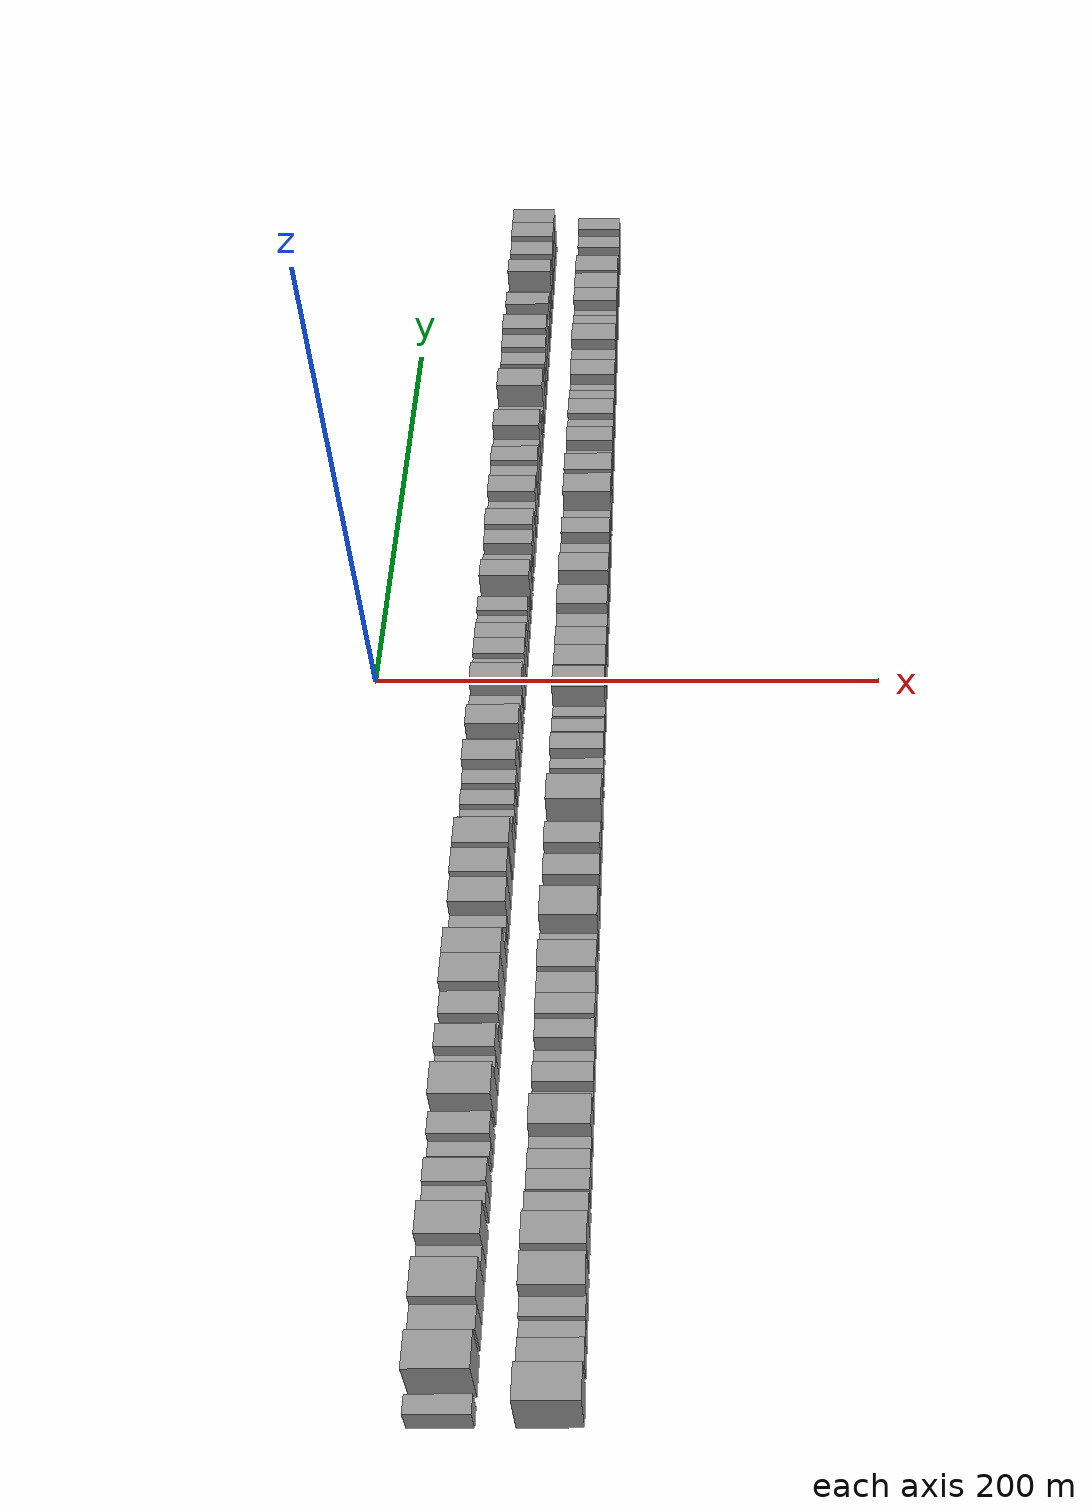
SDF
<sdf version="1.6">
 <world name="default">
  <scene>
   <sky><clouds><speed>12</speed></clouds></sky>
   <ambient>0.4 0.4 0.4 1</ambient>
   <background>0.7 0.7 0.7 1</background>
   <shadows>1</shadows>
  </scene>
  <gravity>0 0 -9.8066</gravity>
  <magnetic_field>6e-06 2.3e-05 -4.2e-05</magnetic_field>
  <physics default="0" name="default_physics" type="ode">
   <ode>
    <solver>
     <type>quick</type>
     <iters>10</iters>
     <sor>1.0</sor>
     <use_dynamic_moi_rescaling>0</use_dynamic_moi_rescaling>
    </solver>
    <constraints>
     <cfm>0</cfm>
     <erp>0.2</erp>
     <contact_max_correcting_vel>100</contact_max_correcting_vel>
     <contact_surface_layer>0.001</contact_surface_layer>
    </constraints>
   </ode>
   <max_step_size>0.004</max_step_size>
   <real_time_factor>1</real_time_factor>
   <real_time_update_rate>250</real_time_update_rate>
  </physics>
  <light name="sun" type="directional">
   <pose>0 0 10 0 0 0</pose>
   <diffuse>0.8 0.8 0.8 1</diffuse>
   <specular>0.2 0.2 0.2 1</specular>
   <attenuation>
    <range>1000</range>
    <constant>0.9</constant>
    <linear>0.01</linear>
    <quadratic>0.001</quadratic>
   </attenuation>
   <direction>-0.5 0.1 -0.9</direction>
  </light>
  <model name="building_1">
   <static>1</static>
   <pose>50.0000 -281.1002 0 0.000000 0.000000 0.000000</pose>
   <link name="link">
    <pose>0 0 6.00 0 0 0</pose>
    <collision name="collision"><geometry><box><size>20.0000 5.7995 12.0000</size></box></geometry></collision>
    <visual name="visual">
     <cast_shadows>0</cast_shadows>
     <geometry><box><size>20.0000 5.7995 12.0000</size></box></geometry>
     <material>
      <script>
       <uri>model://grey_wall/materials/scripts</uri>
       <uri>model://grey_wall/materials/textures</uri>
       <name>vrc/grey_wall</name>
      </script>
     </material>
    </visual>
   </link>
  </model>
  <model name="building_2">
   <static>1</static>
   <pose>50.0000 -269.6048 0 0.000000 0.000000 0.000000</pose>
   <link name="link">
    <pose>0 0 12.00 0 0 0</pose>
    <collision name="collision"><geometry><box><size>20.0000 11.1913 24.0000</size></box></geometry></collision>
    <visual name="visual">
     <cast_shadows>0</cast_shadows>
     <geometry><box><size>20.0000 11.1913 24.0000</size></box></geometry>
     <material>
      <script>
       <uri>model://grey_wall/materials/scripts</uri>
       <uri>model://grey_wall/materials/textures</uri>
       <name>vrc/grey_wall</name>
      </script>
     </material>
    </visual>
   </link>
  </model>
  <model name="building_3">
   <static>1</static>
   <pose>50.0000 -258.2468 0 0.000000 0.000000 0.000000</pose>
   <link name="link">
    <pose>0 0 9.00 0 0 0</pose>
    <collision name="collision"><geometry><box><size>20.0000 7.5247 18.0000</size></box></geometry></collision>
    <visual name="visual">
     <cast_shadows>0</cast_shadows>
     <geometry><box><size>20.0000 7.5247 18.0000</size></box></geometry>
     <material>
      <script>
       <uri>model://grey_wall/materials/scripts</uri>
       <uri>model://grey_wall/materials/textures</uri>
       <name>vrc/grey_wall</name>
      </script>
     </material>
    </visual>
   </link>
  </model>
  <model name="building_4">
   <static>1</static>
   <pose>50.0000 -248.5909 0 0.000000 0.000000 0.000000</pose>
   <link name="link">
    <pose>0 0 12.00 0 0 0</pose>
    <collision name="collision"><geometry><box><size>20.0000 11.7871 24.0000</size></box></geometry></collision>
    <visual name="visual">
     <cast_shadows>0</cast_shadows>
     <geometry><box><size>20.0000 11.7871 24.0000</size></box></geometry>
     <material>
      <script>
       <uri>model://grey_wall/materials/scripts</uri>
       <uri>model://grey_wall/materials/textures</uri>
       <name>vrc/grey_wall</name>
      </script>
     </material>
    </visual>
   </link>
  </model>
  <model name="building_5">
   <static>1</static>
   <pose>50.0000 -239.1604 0 0.000000 0.000000 0.000000</pose>
   <link name="link">
    <pose>0 0 7.50 0 0 0</pose>
    <collision name="collision"><geometry><box><size>20.0000 7.0738 15.0000</size></box></geometry></collision>
    <visual name="visual">
     <cast_shadows>0</cast_shadows>
     <geometry><box><size>20.0000 7.0738 15.0000</size></box></geometry>
     <material>
      <script>
       <uri>model://grey_wall/materials/scripts</uri>
       <uri>model://grey_wall/materials/textures</uri>
       <name>vrc/grey_wall</name>
      </script>
     </material>
    </visual>
   </link>
  </model>
  <model name="building_6">
   <static>1</static>
   <pose>50.0000 -230.5154 0 0.000000 0.000000 0.000000</pose>
   <link name="link">
    <pose>0 0 12.00 0 0 0</pose>
    <collision name="collision"><geometry><box><size>20.0000 10.2162 24.0000</size></box></geometry></collision>
    <visual name="visual">
     <cast_shadows>0</cast_shadows>
     <geometry><box><size>20.0000 10.2162 24.0000</size></box></geometry>
     <material>
      <script>
       <uri>model://grey_wall/materials/scripts</uri>
       <uri>model://grey_wall/materials/textures</uri>
       <name>vrc/grey_wall</name>
      </script>
     </material>
    </visual>
   </link>
  </model>
  <model name="building_7">
   <static>1</static>
   <pose>50.0000 -219.3994 0 0.000000 0.000000 0.000000</pose>
   <link name="link">
    <pose>0 0 7.50 0 0 0</pose>
    <collision name="collision"><geometry><box><size>20.0000 6.0159 15.0000</size></box></geometry></collision>
    <visual name="visual">
     <cast_shadows>0</cast_shadows>
     <geometry><box><size>20.0000 6.0159 15.0000</size></box></geometry>
     <material>
      <script>
       <uri>model://grey_wall/materials/scripts</uri>
       <uri>model://grey_wall/materials/textures</uri>
       <name>vrc/grey_wall</name>
      </script>
     </material>
    </visual>
   </link>
  </model>
  <model name="building_8">
   <static>1</static>
   <pose>50.0000 -212.4667 0 0.000000 0.000000 0.000000</pose>
   <link name="link">
    <pose>0 0 9.00 0 0 0</pose>
    <collision name="collision"><geometry><box><size>20.0000 7.8495 18.0000</size></box></geometry></collision>
    <visual name="visual">
     <cast_shadows>0</cast_shadows>
     <geometry><box><size>20.0000 7.8495 18.0000</size></box></geometry>
     <material>
      <script>
       <uri>model://grey_wall/materials/scripts</uri>
       <uri>model://grey_wall/materials/textures</uri>
       <name>vrc/grey_wall</name>
      </script>
     </material>
    </visual>
   </link>
  </model>
  <model name="building_9">
   <static>1</static>
   <pose>50.0000 -203.0691 0 0.000000 0.000000 0.000000</pose>
   <link name="link">
    <pose>0 0 6.00 0 0 0</pose>
    <collision name="collision"><geometry><box><size>20.0000 4.9457 12.0000</size></box></geometry></collision>
    <visual name="visual">
     <cast_shadows>0</cast_shadows>
     <geometry><box><size>20.0000 4.9457 12.0000</size></box></geometry>
     <material>
      <script>
       <uri>model://grey_wall/materials/scripts</uri>
       <uri>model://grey_wall/materials/textures</uri>
       <name>vrc/grey_wall</name>
      </script>
     </material>
    </visual>
   </link>
  </model>
  <model name="building_10">
   <static>1</static>
   <pose>50.0000 -196.8094 0 0.000000 0.000000 0.000000</pose>
   <link name="link">
    <pose>0 0 9.00 0 0 0</pose>
    <collision name="collision"><geometry><box><size>20.0000 7.5737 18.0000</size></box></geometry></collision>
    <visual name="visual">
     <cast_shadows>0</cast_shadows>
     <geometry><box><size>20.0000 7.5737 18.0000</size></box></geometry>
     <material>
      <script>
       <uri>model://grey_wall/materials/scripts</uri>
       <uri>model://grey_wall/materials/textures</uri>
       <name>vrc/grey_wall</name>
      </script>
     </material>
    </visual>
   </link>
  </model>
  <model name="building_11">
   <static>1</static>
   <pose>50.0000 -184.4767 0 0.000000 0.000000 0.000000</pose>
   <link name="link">
    <pose>0 0 12.00 0 0 0</pose>
    <collision name="collision"><geometry><box><size>20.0000 11.0915 24.0000</size></box></geometry></collision>
    <visual name="visual">
     <cast_shadows>0</cast_shadows>
     <geometry><box><size>20.0000 11.0915 24.0000</size></box></geometry>
     <material>
      <script>
       <uri>model://grey_wall/materials/scripts</uri>
       <uri>model://grey_wall/materials/textures</uri>
       <name>vrc/grey_wall</name>
      </script>
     </material>
    </visual>
   </link>
  </model>
  <model name="building_12">
   <static>1</static>
   <pose>50.0000 -175.4597 0 0.000000 0.000000 0.000000</pose>
   <link name="link">
    <pose>0 0 7.50 0 0 0</pose>
    <collision name="collision"><geometry><box><size>20.0000 6.9426 15.0000</size></box></geometry></collision>
    <visual name="visual">
     <cast_shadows>0</cast_shadows>
     <geometry><box><size>20.0000 6.9426 15.0000</size></box></geometry>
     <material>
      <script>
       <uri>model://grey_wall/materials/scripts</uri>
       <uri>model://grey_wall/materials/textures</uri>
       <name>vrc/grey_wall</name>
      </script>
     </material>
    </visual>
   </link>
  </model>
  <model name="building_13">
   <static>1</static>
   <pose>50.0000 -167.6917 0 0.000000 0.000000 0.000000</pose>
   <link name="link">
    <pose>0 0 10.50 0 0 0</pose>
    <collision name="collision"><geometry><box><size>20.0000 8.5933 21.0000</size></box></geometry></collision>
    <visual name="visual">
     <cast_shadows>0</cast_shadows>
     <geometry><box><size>20.0000 8.5933 21.0000</size></box></geometry>
     <material>
      <script>
       <uri>model://grey_wall/materials/scripts</uri>
       <uri>model://grey_wall/materials/textures</uri>
       <name>vrc/grey_wall</name>
      </script>
     </material>
    </visual>
   </link>
  </model>
  <model name="building_14">
   <static>1</static>
   <pose>50.0000 -160.8005 0 0.000000 0.000000 0.000000</pose>
   <link name="link">
    <pose>0 0 6.00 0 0 0</pose>
    <collision name="collision"><geometry><box><size>20.0000 5.1891 12.0000</size></box></geometry></collision>
    <visual name="visual">
     <cast_shadows>0</cast_shadows>
     <geometry><box><size>20.0000 5.1891 12.0000</size></box></geometry>
     <material>
      <script>
       <uri>model://grey_wall/materials/scripts</uri>
       <uri>model://grey_wall/materials/textures</uri>
       <name>vrc/grey_wall</name>
      </script>
     </material>
    </visual>
   </link>
  </model>
  <model name="building_15">
   <static>1</static>
   <pose>50.0000 -153.9684 0 0.000000 0.000000 0.000000</pose>
   <link name="link">
    <pose>0 0 9.00 0 0 0</pose>
    <collision name="collision"><geometry><box><size>20.0000 8.4751 18.0000</size></box></geometry></collision>
    <visual name="visual">
     <cast_shadows>0</cast_shadows>
     <geometry><box><size>20.0000 8.4751 18.0000</size></box></geometry>
     <material>
      <script>
       <uri>model://grey_wall/materials/scripts</uri>
       <uri>model://grey_wall/materials/textures</uri>
       <name>vrc/grey_wall</name>
      </script>
     </material>
    </visual>
   </link>
  </model>
  <model name="building_16">
   <static>1</static>
   <pose>50.0000 -144.1960 0 0.000000 0.000000 0.000000</pose>
   <link name="link">
    <pose>0 0 12.00 0 0 0</pose>
    <collision name="collision"><geometry><box><size>20.0000 11.0698 24.0000</size></box></geometry></collision>
    <visual name="visual">
     <cast_shadows>0</cast_shadows>
     <geometry><box><size>20.0000 11.0698 24.0000</size></box></geometry>
     <material>
      <script>
       <uri>model://grey_wall/materials/scripts</uri>
       <uri>model://grey_wall/materials/textures</uri>
       <name>vrc/grey_wall</name>
      </script>
     </material>
    </visual>
   </link>
  </model>
  <model name="building_17">
   <static>1</static>
   <pose>50.0000 -133.6998 0 0.000000 0.000000 0.000000</pose>
   <link name="link">
    <pose>0 0 12.00 0 0 0</pose>
    <collision name="collision"><geometry><box><size>20.0000 9.9225 24.0000</size></box></geometry></collision>
    <visual name="visual">
     <cast_shadows>0</cast_shadows>
     <geometry><box><size>20.0000 9.9225 24.0000</size></box></geometry>
     <material>
      <script>
       <uri>model://grey_wall/materials/scripts</uri>
       <uri>model://grey_wall/materials/textures</uri>
       <name>vrc/grey_wall</name>
      </script>
     </material>
    </visual>
   </link>
  </model>
  <model name="building_18">
   <static>1</static>
   <pose>50.0000 -126.0071 0 0.000000 0.000000 0.000000</pose>
   <link name="link">
    <pose>0 0 6.00 0 0 0</pose>
    <collision name="collision"><geometry><box><size>20.0000 5.4629 12.0000</size></box></geometry></collision>
    <visual name="visual">
     <cast_shadows>0</cast_shadows>
     <geometry><box><size>20.0000 5.4629 12.0000</size></box></geometry>
     <material>
      <script>
       <uri>model://grey_wall/materials/scripts</uri>
       <uri>model://grey_wall/materials/textures</uri>
       <name>vrc/grey_wall</name>
      </script>
     </material>
    </visual>
   </link>
  </model>
  <model name="building_19">
   <static>1</static>
   <pose>50.0000 -118.8650 0 0.000000 0.000000 0.000000</pose>
   <link name="link">
    <pose>0 0 6.00 0 0 0</pose>
    <collision name="collision"><geometry><box><size>20.0000 4.8213 12.0000</size></box></geometry></collision>
    <visual name="visual">
     <cast_shadows>0</cast_shadows>
     <geometry><box><size>20.0000 4.8213 12.0000</size></box></geometry>
     <material>
      <script>
       <uri>model://grey_wall/materials/scripts</uri>
       <uri>model://grey_wall/materials/textures</uri>
       <name>vrc/grey_wall</name>
      </script>
     </material>
    </visual>
   </link>
  </model>
  <model name="building_20">
   <static>1</static>
   <pose>50.0000 -111.2466 0 0.000000 0.000000 0.000000</pose>
   <link name="link">
    <pose>0 0 10.50 0 0 0</pose>
    <collision name="collision"><geometry><box><size>20.0000 10.4155 21.0000</size></box></geometry></collision>
    <visual name="visual">
     <cast_shadows>0</cast_shadows>
     <geometry><box><size>20.0000 10.4155 21.0000</size></box></geometry>
     <material>
      <script>
       <uri>model://grey_wall/materials/scripts</uri>
       <uri>model://grey_wall/materials/textures</uri>
       <name>vrc/grey_wall</name>
      </script>
     </material>
    </visual>
   </link>
  </model>
  <model name="building_21">
   <static>1</static>
   <pose>50.0000 -100.9907 0 0.000000 0.000000 0.000000</pose>
   <link name="link">
    <pose>0 0 12.00 0 0 0</pose>
    <collision name="collision"><geometry><box><size>20.0000 10.0962 24.0000</size></box></geometry></collision>
    <visual name="visual">
     <cast_shadows>0</cast_shadows>
     <geometry><box><size>20.0000 10.0962 24.0000</size></box></geometry>
     <material>
      <script>
       <uri>model://grey_wall/materials/scripts</uri>
       <uri>model://grey_wall/materials/textures</uri>
       <name>vrc/grey_wall</name>
      </script>
     </material>
    </visual>
   </link>
  </model>
  <model name="building_22">
   <static>1</static>
   <pose>50.0000 -88.4051 0 0.000000 0.000000 0.000000</pose>
   <link name="link">
    <pose>0 0 12.00 0 0 0</pose>
    <collision name="collision"><geometry><box><size>20.0000 11.0750 24.0000</size></box></geometry></collision>
    <visual name="visual">
     <cast_shadows>0</cast_shadows>
     <geometry><box><size>20.0000 11.0750 24.0000</size></box></geometry>
     <material>
      <script>
       <uri>model://grey_wall/materials/scripts</uri>
       <uri>model://grey_wall/materials/textures</uri>
       <name>vrc/grey_wall</name>
      </script>
     </material>
    </visual>
   </link>
  </model>
  <model name="building_23">
   <static>1</static>
   <pose>50.0000 -79.4754 0 0.000000 0.000000 0.000000</pose>
   <link name="link">
    <pose>0 0 7.50 0 0 0</pose>
    <collision name="collision"><geometry><box><size>20.0000 6.7845 15.0000</size></box></geometry></collision>
    <visual name="visual">
     <cast_shadows>0</cast_shadows>
     <geometry><box><size>20.0000 6.7845 15.0000</size></box></geometry>
     <material>
      <script>
       <uri>model://grey_wall/materials/scripts</uri>
       <uri>model://grey_wall/materials/textures</uri>
       <name>vrc/grey_wall</name>
      </script>
     </material>
    </visual>
   </link>
  </model>
  <model name="building_24">
   <static>1</static>
   <pose>50.0000 -73.4799 0 0.000000 0.000000 0.000000</pose>
   <link name="link">
    <pose>0 0 6.00 0 0 0</pose>
    <collision name="collision"><geometry><box><size>20.0000 5.2065 12.0000</size></box></geometry></collision>
    <visual name="visual">
     <cast_shadows>0</cast_shadows>
     <geometry><box><size>20.0000 5.2065 12.0000</size></box></geometry>
     <material>
      <script>
       <uri>model://grey_wall/materials/scripts</uri>
       <uri>model://grey_wall/materials/textures</uri>
       <name>vrc/grey_wall</name>
      </script>
     </material>
    </visual>
   </link>
  </model>
  <model name="building_25">
   <static>1</static>
   <pose>50.0000 -67.5074 0 0.000000 0.000000 0.000000</pose>
   <link name="link">
    <pose>0 0 7.50 0 0 0</pose>
    <collision name="collision"><geometry><box><size>20.0000 6.7385 15.0000</size></box></geometry></collision>
    <visual name="visual">
     <cast_shadows>0</cast_shadows>
     <geometry><box><size>20.0000 6.7385 15.0000</size></box></geometry>
     <material>
      <script>
       <uri>model://grey_wall/materials/scripts</uri>
       <uri>model://grey_wall/materials/textures</uri>
       <name>vrc/grey_wall</name>
      </script>
     </material>
    </visual>
   </link>
  </model>
  <model name="building_26">
   <static>1</static>
   <pose>50.0000 -57.9240 0 0.000000 0.000000 0.000000</pose>
   <link name="link">
    <pose>0 0 7.50 0 0 0</pose>
    <collision name="collision"><geometry><box><size>20.0000 6.4283 15.0000</size></box></geometry></collision>
    <visual name="visual">
     <cast_shadows>0</cast_shadows>
     <geometry><box><size>20.0000 6.4283 15.0000</size></box></geometry>
     <material>
      <script>
       <uri>model://grey_wall/materials/scripts</uri>
       <uri>model://grey_wall/materials/textures</uri>
       <name>vrc/grey_wall</name>
      </script>
     </material>
    </visual>
   </link>
  </model>
  <model name="building_27">
   <static>1</static>
   <pose>50.0000 -50.0287 0 0.000000 0.000000 0.000000</pose>
   <link name="link">
    <pose>0 0 10.50 0 0 0</pose>
    <collision name="collision"><geometry><box><size>20.0000 9.3624 21.0000</size></box></geometry></collision>
    <visual name="visual">
     <cast_shadows>0</cast_shadows>
     <geometry><box><size>20.0000 9.3624 21.0000</size></box></geometry>
     <material>
      <script>
       <uri>model://grey_wall/materials/scripts</uri>
       <uri>model://grey_wall/materials/textures</uri>
       <name>vrc/grey_wall</name>
      </script>
     </material>
    </visual>
   </link>
  </model>
  <model name="building_28">
   <static>1</static>
   <pose>50.0000 -40.5329 0 0.000000 0.000000 0.000000</pose>
   <link name="link">
    <pose>0 0 6.00 0 0 0</pose>
    <collision name="collision"><geometry><box><size>20.0000 5.6292 12.0000</size></box></geometry></collision>
    <visual name="visual">
     <cast_shadows>0</cast_shadows>
     <geometry><box><size>20.0000 5.6292 12.0000</size></box></geometry>
     <material>
      <script>
       <uri>model://grey_wall/materials/scripts</uri>
       <uri>model://grey_wall/materials/textures</uri>
       <name>vrc/grey_wall</name>
      </script>
     </material>
    </visual>
   </link>
  </model>
  <model name="building_29">
   <static>1</static>
   <pose>50.0000 -33.0718 0 0.000000 0.000000 0.000000</pose>
   <link name="link">
    <pose>0 0 10.50 0 0 0</pose>
    <collision name="collision"><geometry><box><size>20.0000 9.2932 21.0000</size></box></geometry></collision>
    <visual name="visual">
     <cast_shadows>0</cast_shadows>
     <geometry><box><size>20.0000 9.2932 21.0000</size></box></geometry>
     <material>
      <script>
       <uri>model://grey_wall/materials/scripts</uri>
       <uri>model://grey_wall/materials/textures</uri>
       <name>vrc/grey_wall</name>
      </script>
     </material>
    </visual>
   </link>
  </model>
  <model name="building_30">
   <static>1</static>
   <pose>50.0000 -22.9545 0 0.000000 0.000000 0.000000</pose>
   <link name="link">
    <pose>0 0 7.50 0 0 0</pose>
    <collision name="collision"><geometry><box><size>20.0000 6.9413 15.0000</size></box></geometry></collision>
    <visual name="visual">
     <cast_shadows>0</cast_shadows>
     <geometry><box><size>20.0000 6.9413 15.0000</size></box></geometry>
     <material>
      <script>
       <uri>model://grey_wall/materials/scripts</uri>
       <uri>model://grey_wall/materials/textures</uri>
       <name>vrc/grey_wall</name>
      </script>
     </material>
    </visual>
   </link>
  </model>
  <model name="building_31">
   <static>1</static>
   <pose>50.0000 -11.9963 0 0.000000 0.000000 0.000000</pose>
   <link name="link">
    <pose>0 0 10.50 0 0 0</pose>
    <collision name="collision"><geometry><box><size>20.0000 8.9750 21.0000</size></box></geometry></collision>
    <visual name="visual">
     <cast_shadows>0</cast_shadows>
     <geometry><box><size>20.0000 8.9750 21.0000</size></box></geometry>
     <material>
      <script>
       <uri>model://grey_wall/materials/scripts</uri>
       <uri>model://grey_wall/materials/textures</uri>
       <name>vrc/grey_wall</name>
      </script>
     </material>
    </visual>
   </link>
  </model>
  <model name="building_32">
   <static>1</static>
   <pose>50.0000 -4.1049 0 0.000000 0.000000 0.000000</pose>
   <link name="link">
    <pose>0 0 7.50 0 0 0</pose>
    <collision name="collision"><geometry><box><size>20.0000 6.8079 15.0000</size></box></geometry></collision>
    <visual name="visual">
     <cast_shadows>0</cast_shadows>
     <geometry><box><size>20.0000 6.8079 15.0000</size></box></geometry>
     <material>
      <script>
       <uri>model://grey_wall/materials/scripts</uri>
       <uri>model://grey_wall/materials/textures</uri>
       <name>vrc/grey_wall</name>
      </script>
     </material>
    </visual>
   </link>
  </model>
  <model name="building_33">
   <static>1</static>
   <pose>50.0000 3.5767 0 0.000000 0.000000 0.000000</pose>
   <link name="link">
    <pose>0 0 9.00 0 0 0</pose>
    <collision name="collision"><geometry><box><size>20.0000 8.5552 18.0000</size></box></geometry></collision>
    <visual name="visual">
     <cast_shadows>0</cast_shadows>
     <geometry><box><size>20.0000 8.5552 18.0000</size></box></geometry>
     <material>
      <script>
       <uri>model://grey_wall/materials/scripts</uri>
       <uri>model://grey_wall/materials/textures</uri>
       <name>vrc/grey_wall</name>
      </script>
     </material>
    </visual>
   </link>
  </model>
  <model name="building_34">
   <static>1</static>
   <pose>50.0000 11.8458 0 0.000000 0.000000 0.000000</pose>
   <link name="link">
    <pose>0 0 9.00 0 0 0</pose>
    <collision name="collision"><geometry><box><size>20.0000 7.9831 18.0000</size></box></geometry></collision>
    <visual name="visual">
     <cast_shadows>0</cast_shadows>
     <geometry><box><size>20.0000 7.9831 18.0000</size></box></geometry>
     <material>
      <script>
       <uri>model://grey_wall/materials/scripts</uri>
       <uri>model://grey_wall/materials/textures</uri>
       <name>vrc/grey_wall</name>
      </script>
     </material>
    </visual>
   </link>
  </model>
  <model name="building_35">
   <static>1</static>
   <pose>50.0000 18.9449 0 0.000000 0.000000 0.000000</pose>
   <link name="link">
    <pose>0 0 7.50 0 0 0</pose>
    <collision name="collision"><geometry><box><size>20.0000 6.2151 15.0000</size></box></geometry></collision>
    <visual name="visual">
     <cast_shadows>0</cast_shadows>
     <geometry><box><size>20.0000 6.2151 15.0000</size></box></geometry>
     <material>
      <script>
       <uri>model://grey_wall/materials/scripts</uri>
       <uri>model://grey_wall/materials/textures</uri>
       <name>vrc/grey_wall</name>
      </script>
     </material>
    </visual>
   </link>
  </model>
  <model name="building_36">
   <static>1</static>
   <pose>50.0000 25.9649 0 0.000000 0.000000 0.000000</pose>
   <link name="link">
    <pose>0 0 9.00 0 0 0</pose>
    <collision name="collision"><geometry><box><size>20.0000 7.8249 18.0000</size></box></geometry></collision>
    <visual name="visual">
     <cast_shadows>0</cast_shadows>
     <geometry><box><size>20.0000 7.8249 18.0000</size></box></geometry>
     <material>
      <script>
       <uri>model://grey_wall/materials/scripts</uri>
       <uri>model://grey_wall/materials/textures</uri>
       <name>vrc/grey_wall</name>
      </script>
     </material>
    </visual>
   </link>
  </model>
  <model name="building_37">
   <static>1</static>
   <pose>50.0000 32.6095 0 0.000000 0.000000 0.000000</pose>
   <link name="link">
    <pose>0 0 6.00 0 0 0</pose>
    <collision name="collision"><geometry><box><size>20.0000 5.4643 12.0000</size></box></geometry></collision>
    <visual name="visual">
     <cast_shadows>0</cast_shadows>
     <geometry><box><size>20.0000 5.4643 12.0000</size></box></geometry>
     <material>
      <script>
       <uri>model://grey_wall/materials/scripts</uri>
       <uri>model://grey_wall/materials/textures</uri>
       <name>vrc/grey_wall</name>
      </script>
     </material>
    </visual>
   </link>
  </model>
  <model name="building_38">
   <static>1</static>
   <pose>50.0000 42.9192 0 0.000000 0.000000 0.000000</pose>
   <link name="link">
    <pose>0 0 10.50 0 0 0</pose>
    <collision name="collision"><geometry><box><size>20.0000 9.1551 21.0000</size></box></geometry></collision>
    <visual name="visual">
     <cast_shadows>0</cast_shadows>
     <geometry><box><size>20.0000 9.1551 21.0000</size></box></geometry>
     <material>
      <script>
       <uri>model://grey_wall/materials/scripts</uri>
       <uri>model://grey_wall/materials/textures</uri>
       <name>vrc/grey_wall</name>
      </script>
     </material>
    </visual>
   </link>
  </model>
  <model name="building_39">
   <static>1</static>
   <pose>50.0000 52.9085 0 0.000000 0.000000 0.000000</pose>
   <link name="link">
    <pose>0 0 7.50 0 0 0</pose>
    <collision name="collision"><geometry><box><size>20.0000 6.8234 15.0000</size></box></geometry></collision>
    <visual name="visual">
     <cast_shadows>0</cast_shadows>
     <geometry><box><size>20.0000 6.8234 15.0000</size></box></geometry>
     <material>
      <script>
       <uri>model://grey_wall/materials/scripts</uri>
       <uri>model://grey_wall/materials/textures</uri>
       <name>vrc/grey_wall</name>
      </script>
     </material>
    </visual>
   </link>
  </model>
  <model name="building_40">
   <static>1</static>
   <pose>50.0000 63.4467 0 0.000000 0.000000 0.000000</pose>
   <link name="link">
    <pose>0 0 9.00 0 0 0</pose>
    <collision name="collision"><geometry><box><size>20.0000 8.2529 18.0000</size></box></geometry></collision>
    <visual name="visual">
     <cast_shadows>0</cast_shadows>
     <geometry><box><size>20.0000 8.2529 18.0000</size></box></geometry>
     <material>
      <script>
       <uri>model://grey_wall/materials/scripts</uri>
       <uri>model://grey_wall/materials/textures</uri>
       <name>vrc/grey_wall</name>
      </script>
     </material>
    </visual>
   </link>
  </model>
  <model name="building_41">
   <static>1</static>
   <pose>50.0000 72.3110 0 0.000000 0.000000 0.000000</pose>
   <link name="link">
    <pose>0 0 10.50 0 0 0</pose>
    <collision name="collision"><geometry><box><size>20.0000 9.4759 21.0000</size></box></geometry></collision>
    <visual name="visual">
     <cast_shadows>0</cast_shadows>
     <geometry><box><size>20.0000 9.4759 21.0000</size></box></geometry>
     <material>
      <script>
       <uri>model://grey_wall/materials/scripts</uri>
       <uri>model://grey_wall/materials/textures</uri>
       <name>vrc/grey_wall</name>
      </script>
     </material>
    </visual>
   </link>
  </model>
  <model name="building_42">
   <static>1</static>
   <pose>50.0000 83.6777 0 0.000000 0.000000 0.000000</pose>
   <link name="link">
    <pose>0 0 7.50 0 0 0</pose>
    <collision name="collision"><geometry><box><size>20.0000 7.2575 15.0000</size></box></geometry></collision>
    <visual name="visual">
     <cast_shadows>0</cast_shadows>
     <geometry><box><size>20.0000 7.2575 15.0000</size></box></geometry>
     <material>
      <script>
       <uri>model://grey_wall/materials/scripts</uri>
       <uri>model://grey_wall/materials/textures</uri>
       <name>vrc/grey_wall</name>
      </script>
     </material>
    </visual>
   </link>
  </model>
  <model name="building_43">
   <static>1</static>
   <pose>50.0000 92.1425 0 0.000000 0.000000 0.000000</pose>
   <link name="link">
    <pose>0 0 10.50 0 0 0</pose>
    <collision name="collision"><geometry><box><size>20.0000 9.6722 21.0000</size></box></geometry></collision>
    <visual name="visual">
     <cast_shadows>0</cast_shadows>
     <geometry><box><size>20.0000 9.6722 21.0000</size></box></geometry>
     <material>
      <script>
       <uri>model://grey_wall/materials/scripts</uri>
       <uri>model://grey_wall/materials/textures</uri>
       <name>vrc/grey_wall</name>
      </script>
     </material>
    </visual>
   </link>
  </model>
  <model name="building_44">
   <static>1</static>
   <pose>50.0000 102.6468 0 0.000000 0.000000 0.000000</pose>
   <link name="link">
    <pose>0 0 9.00 0 0 0</pose>
    <collision name="collision"><geometry><box><size>20.0000 7.3364 18.0000</size></box></geometry></collision>
    <visual name="visual">
     <cast_shadows>0</cast_shadows>
     <geometry><box><size>20.0000 7.3364 18.0000</size></box></geometry>
     <material>
      <script>
       <uri>model://grey_wall/materials/scripts</uri>
       <uri>model://grey_wall/materials/textures</uri>
       <name>vrc/grey_wall</name>
      </script>
     </material>
    </visual>
   </link>
  </model>
  <model name="building_45">
   <static>1</static>
   <pose>50.0000 110.8877 0 0.000000 0.000000 0.000000</pose>
   <link name="link">
    <pose>0 0 10.50 0 0 0</pose>
    <collision name="collision"><geometry><box><size>20.0000 9.1454 21.0000</size></box></geometry></collision>
    <visual name="visual">
     <cast_shadows>0</cast_shadows>
     <geometry><box><size>20.0000 9.1454 21.0000</size></box></geometry>
     <material>
      <script>
       <uri>model://grey_wall/materials/scripts</uri>
       <uri>model://grey_wall/materials/textures</uri>
       <name>vrc/grey_wall</name>
      </script>
     </material>
    </visual>
   </link>
  </model>
  <model name="building_46">
   <static>1</static>
   <pose>50.0000 119.2314 0 0.000000 0.000000 0.000000</pose>
   <link name="link">
    <pose>0 0 9.00 0 0 0</pose>
    <collision name="collision"><geometry><box><size>20.0000 7.5420 18.0000</size></box></geometry></collision>
    <visual name="visual">
     <cast_shadows>0</cast_shadows>
     <geometry><box><size>20.0000 7.5420 18.0000</size></box></geometry>
     <material>
      <script>
       <uri>model://grey_wall/materials/scripts</uri>
       <uri>model://grey_wall/materials/textures</uri>
       <name>vrc/grey_wall</name>
      </script>
     </material>
    </visual>
   </link>
  </model>
  <model name="building_47">
   <static>1</static>
   <pose>50.0000 130.3996 0 0.000000 0.000000 0.000000</pose>
   <link name="link">
    <pose>0 0 12.00 0 0 0</pose>
    <collision name="collision"><geometry><box><size>20.0000 10.7944 24.0000</size></box></geometry></collision>
    <visual name="visual">
     <cast_shadows>0</cast_shadows>
     <geometry><box><size>20.0000 10.7944 24.0000</size></box></geometry>
     <material>
      <script>
       <uri>model://grey_wall/materials/scripts</uri>
       <uri>model://grey_wall/materials/textures</uri>
       <name>vrc/grey_wall</name>
      </script>
     </material>
    </visual>
   </link>
  </model>
  <model name="building_48">
   <static>1</static>
   <pose>50.0000 141.2876 0 0.000000 0.000000 0.000000</pose>
   <link name="link">
    <pose>0 0 7.50 0 0 0</pose>
    <collision name="collision"><geometry><box><size>20.0000 6.9815 15.0000</size></box></geometry></collision>
    <visual name="visual">
     <cast_shadows>0</cast_shadows>
     <geometry><box><size>20.0000 6.9815 15.0000</size></box></geometry>
     <material>
      <script>
       <uri>model://grey_wall/materials/scripts</uri>
       <uri>model://grey_wall/materials/textures</uri>
       <name>vrc/grey_wall</name>
      </script>
     </material>
    </visual>
   </link>
  </model>
  <model name="building_49">
   <static>1</static>
   <pose>50.0000 149.2749 0 0.000000 0.000000 0.000000</pose>
   <link name="link">
    <pose>0 0 6.00 0 0 0</pose>
    <collision name="collision"><geometry><box><size>20.0000 4.9933 12.0000</size></box></geometry></collision>
    <visual name="visual">
     <cast_shadows>0</cast_shadows>
     <geometry><box><size>20.0000 4.9933 12.0000</size></box></geometry>
     <material>
      <script>
       <uri>model://grey_wall/materials/scripts</uri>
       <uri>model://grey_wall/materials/textures</uri>
       <name>vrc/grey_wall</name>
      </script>
     </material>
    </visual>
   </link>
  </model>
  <model name="building_50">
   <static>1</static>
   <pose>50.0000 157.6174 0 0.000000 0.000000 0.000000</pose>
   <link name="link">
    <pose>0 0 12.00 0 0 0</pose>
    <collision name="collision"><geometry><box><size>20.0000 11.6915 24.0000</size></box></geometry></collision>
    <visual name="visual">
     <cast_shadows>0</cast_shadows>
     <geometry><box><size>20.0000 11.6915 24.0000</size></box></geometry>
     <material>
      <script>
       <uri>model://grey_wall/materials/scripts</uri>
       <uri>model://grey_wall/materials/textures</uri>
       <name>vrc/grey_wall</name>
      </script>
     </material>
    </visual>
   </link>
  </model>
  <model name="building_51">
   <static>1</static>
   <pose>50.0000 167.3850 0 0.000000 0.000000 0.000000</pose>
   <link name="link">
    <pose>0 0 9.00 0 0 0</pose>
    <collision name="collision"><geometry><box><size>20.0000 7.8438 18.0000</size></box></geometry></collision>
    <visual name="visual">
     <cast_shadows>0</cast_shadows>
     <geometry><box><size>20.0000 7.8438 18.0000</size></box></geometry>
     <material>
      <script>
       <uri>model://grey_wall/materials/scripts</uri>
       <uri>model://grey_wall/materials/textures</uri>
       <name>vrc/grey_wall</name>
      </script>
     </material>
    </visual>
   </link>
  </model>
  <model name="building_52">
   <static>1</static>
   <pose>50.0000 177.6294 0 0.000000 0.000000 0.000000</pose>
   <link name="link">
    <pose>0 0 9.00 0 0 0</pose>
    <collision name="collision"><geometry><box><size>20.0000 8.6449 18.0000</size></box></geometry></collision>
    <visual name="visual">
     <cast_shadows>0</cast_shadows>
     <geometry><box><size>20.0000 8.6449 18.0000</size></box></geometry>
     <material>
      <script>
       <uri>model://grey_wall/materials/scripts</uri>
       <uri>model://grey_wall/materials/textures</uri>
       <name>vrc/grey_wall</name>
      </script>
     </material>
    </visual>
   </link>
  </model>
  <model name="building_53">
   <static>1</static>
   <pose>50.0000 186.6931 0 0.000000 0.000000 0.000000</pose>
   <link name="link">
    <pose>0 0 10.50 0 0 0</pose>
    <collision name="collision"><geometry><box><size>20.0000 9.4825 21.0000</size></box></geometry></collision>
    <visual name="visual">
     <cast_shadows>0</cast_shadows>
     <geometry><box><size>20.0000 9.4825 21.0000</size></box></geometry>
     <material>
      <script>
       <uri>model://grey_wall/materials/scripts</uri>
       <uri>model://grey_wall/materials/textures</uri>
       <name>vrc/grey_wall</name>
      </script>
     </material>
    </visual>
   </link>
  </model>
  <model name="building_54">
   <static>1</static>
   <pose>50.0000 196.7727 0 0.000000 0.000000 0.000000</pose>
   <link name="link">
    <pose>0 0 12.00 0 0 0</pose>
    <collision name="collision"><geometry><box><size>20.0000 10.6767 24.0000</size></box></geometry></collision>
    <visual name="visual">
     <cast_shadows>0</cast_shadows>
     <geometry><box><size>20.0000 10.6767 24.0000</size></box></geometry>
     <material>
      <script>
       <uri>model://grey_wall/materials/scripts</uri>
       <uri>model://grey_wall/materials/textures</uri>
       <name>vrc/grey_wall</name>
      </script>
     </material>
    </visual>
   </link>
  </model>
  <model name="building_55">
   <static>1</static>
   <pose>50.0000 204.8841 0 0.000000 0.000000 0.000000</pose>
   <link name="link">
    <pose>0 0 6.00 0 0 0</pose>
    <collision name="collision"><geometry><box><size>20.0000 5.5460 12.0000</size></box></geometry></collision>
    <visual name="visual">
     <cast_shadows>0</cast_shadows>
     <geometry><box><size>20.0000 5.5460 12.0000</size></box></geometry>
     <material>
      <script>
       <uri>model://grey_wall/materials/scripts</uri>
       <uri>model://grey_wall/materials/textures</uri>
       <name>vrc/grey_wall</name>
      </script>
     </material>
    </visual>
   </link>
  </model>
  <model name="building_56">
   <static>1</static>
   <pose>50.0000 210.6251 0 0.000000 0.000000 0.000000</pose>
   <link name="link">
    <pose>0 0 6.00 0 0 0</pose>
    <collision name="collision"><geometry><box><size>20.0000 5.9360 12.0000</size></box></geometry></collision>
    <visual name="visual">
     <cast_shadows>0</cast_shadows>
     <geometry><box><size>20.0000 5.9360 12.0000</size></box></geometry>
     <material>
      <script>
       <uri>model://grey_wall/materials/scripts</uri>
       <uri>model://grey_wall/materials/textures</uri>
       <name>vrc/grey_wall</name>
      </script>
     </material>
    </visual>
   </link>
  </model>
  <model name="building_57">
   <static>1</static>
   <pose>50.0000 217.8418 0 0.000000 0.000000 0.000000</pose>
   <link name="link">
    <pose>0 0 10.50 0 0 0</pose>
    <collision name="collision"><geometry><box><size>20.0000 8.4974 21.0000</size></box></geometry></collision>
    <visual name="visual">
     <cast_shadows>0</cast_shadows>
     <geometry><box><size>20.0000 8.4974 21.0000</size></box></geometry>
     <material>
      <script>
       <uri>model://grey_wall/materials/scripts</uri>
       <uri>model://grey_wall/materials/textures</uri>
       <name>vrc/grey_wall</name>
      </script>
     </material>
    </visual>
   </link>
  </model>
  <model name="building_58">
   <static>1</static>
   <pose>50.0000 227.5910 0 0.000000 0.000000 0.000000</pose>
   <link name="link">
    <pose>0 0 7.50 0 0 0</pose>
    <collision name="collision"><geometry><box><size>20.0000 7.0010 15.0000</size></box></geometry></collision>
    <visual name="visual">
     <cast_shadows>0</cast_shadows>
     <geometry><box><size>20.0000 7.0010 15.0000</size></box></geometry>
     <material>
      <script>
       <uri>model://grey_wall/materials/scripts</uri>
       <uri>model://grey_wall/materials/textures</uri>
       <name>vrc/grey_wall</name>
      </script>
     </material>
    </visual>
   </link>
  </model>
  <model name="building_59">
   <static>1</static>
   <pose>50.0000 238.9866 0 0.000000 0.000000 0.000000</pose>
   <link name="link">
    <pose>0 0 12.00 0 0 0</pose>
    <collision name="collision"><geometry><box><size>20.0000 9.7903 24.0000</size></box></geometry></collision>
    <visual name="visual">
     <cast_shadows>0</cast_shadows>
     <geometry><box><size>20.0000 9.7903 24.0000</size></box></geometry>
     <material>
      <script>
       <uri>model://grey_wall/materials/scripts</uri>
       <uri>model://grey_wall/materials/textures</uri>
       <name>vrc/grey_wall</name>
      </script>
     </material>
    </visual>
   </link>
  </model>
  <model name="building_60">
   <static>1</static>
   <pose>50.0000 246.9632 0 0.000000 0.000000 0.000000</pose>
   <link name="link">
    <pose>0 0 7.50 0 0 0</pose>
    <collision name="collision"><geometry><box><size>20.0000 6.1629 15.0000</size></box></geometry></collision>
    <visual name="visual">
     <cast_shadows>0</cast_shadows>
     <geometry><box><size>20.0000 6.1629 15.0000</size></box></geometry>
     <material>
      <script>
       <uri>model://grey_wall/materials/scripts</uri>
       <uri>model://grey_wall/materials/textures</uri>
       <name>vrc/grey_wall</name>
      </script>
     </material>
    </visual>
   </link>
  </model>
  <model name="building_61">
   <static>1</static>
   <pose>50.0000 257.2589 0 0.000000 0.000000 0.000000</pose>
   <link name="link">
    <pose>0 0 10.50 0 0 0</pose>
    <collision name="collision"><geometry><box><size>20.0000 10.4286 21.0000</size></box></geometry></collision>
    <visual name="visual">
     <cast_shadows>0</cast_shadows>
     <geometry><box><size>20.0000 10.4286 21.0000</size></box></geometry>
     <material>
      <script>
       <uri>model://grey_wall/materials/scripts</uri>
       <uri>model://grey_wall/materials/textures</uri>
       <name>vrc/grey_wall</name>
      </script>
     </material>
    </visual>
   </link>
  </model>
  <model name="building_62">
   <static>1</static>
   <pose>50.0000 267.9536 0 0.000000 0.000000 0.000000</pose>
   <link name="link">
    <pose>0 0 12.00 0 0 0</pose>
    <collision name="collision"><geometry><box><size>20.0000 10.9608 24.0000</size></box></geometry></collision>
    <visual name="visual">
     <cast_shadows>0</cast_shadows>
     <geometry><box><size>20.0000 10.9608 24.0000</size></box></geometry>
     <material>
      <script>
       <uri>model://grey_wall/materials/scripts</uri>
       <uri>model://grey_wall/materials/textures</uri>
       <name>vrc/grey_wall</name>
      </script>
     </material>
    </visual>
   </link>
  </model>
  <model name="building_63">
   <static>1</static>
   <pose>50.0000 278.7826 0 0.000000 0.000000 0.000000</pose>
   <link name="link">
    <pose>0 0 12.00 0 0 0</pose>
    <collision name="collision"><geometry><box><size>20.0000 10.6971 24.0000</size></box></geometry></collision>
    <visual name="visual">
     <cast_shadows>0</cast_shadows>
     <geometry><box><size>20.0000 10.6971 24.0000</size></box></geometry>
     <material>
      <script>
       <uri>model://grey_wall/materials/scripts</uri>
       <uri>model://grey_wall/materials/textures</uri>
       <name>vrc/grey_wall</name>
      </script>
     </material>
    </visual>
   </link>
  </model>
  <model name="building_64">
   <static>1</static>
   <pose>82.0000 -278.6388 0 0.000000 0.000000 0.000000</pose>
   <link name="link">
    <pose>0 0 12.00 0 0 0</pose>
    <collision name="collision"><geometry><box><size>20.0000 10.7223 24.0000</size></box></geometry></collision>
    <visual name="visual">
     <cast_shadows>0</cast_shadows>
     <geometry><box><size>20.0000 10.7223 24.0000</size></box></geometry>
     <material>
      <script>
       <uri>model://grey_wall/materials/scripts</uri>
       <uri>model://grey_wall/materials/textures</uri>
       <name>vrc/grey_wall</name>
      </script>
     </material>
    </visual>
   </link>
  </model>
  <model name="building_65">
   <static>1</static>
   <pose>82.0000 -266.6919 0 0.000000 0.000000 0.000000</pose>
   <link name="link">
    <pose>0 0 7.50 0 0 0</pose>
    <collision name="collision"><geometry><box><size>20.0000 7.1716 15.0000</size></box></geometry></collision>
    <visual name="visual">
     <cast_shadows>0</cast_shadows>
     <geometry><box><size>20.0000 7.1716 15.0000</size></box></geometry>
     <material>
      <script>
       <uri>model://grey_wall/materials/scripts</uri>
       <uri>model://grey_wall/materials/textures</uri>
       <name>vrc/grey_wall</name>
      </script>
     </material>
    </visual>
   </link>
  </model>
  <model name="building_66">
   <static>1</static>
   <pose>82.0000 -260.1304 0 0.000000 0.000000 0.000000</pose>
   <link name="link">
    <pose>0 0 6.00 0 0 0</pose>
    <collision name="collision"><geometry><box><size>20.0000 5.9513 12.0000</size></box></geometry></collision>
    <visual name="visual">
     <cast_shadows>0</cast_shadows>
     <geometry><box><size>20.0000 5.9513 12.0000</size></box></geometry>
     <material>
      <script>
       <uri>model://grey_wall/materials/scripts</uri>
       <uri>model://grey_wall/materials/textures</uri>
       <name>vrc/grey_wall</name>
      </script>
     </material>
    </visual>
   </link>
  </model>
  <model name="building_67">
   <static>1</static>
   <pose>82.0000 -254.0989 0 0.000000 0.000000 0.000000</pose>
   <link name="link">
    <pose>0 0 7.50 0 0 0</pose>
    <collision name="collision"><geometry><box><size>20.0000 6.1117 15.0000</size></box></geometry></collision>
    <visual name="visual">
     <cast_shadows>0</cast_shadows>
     <geometry><box><size>20.0000 6.1117 15.0000</size></box></geometry>
     <material>
      <script>
       <uri>model://grey_wall/materials/scripts</uri>
       <uri>model://grey_wall/materials/textures</uri>
       <name>vrc/grey_wall</name>
      </script>
     </material>
    </visual>
   </link>
  </model>
  <model name="building_68">
   <static>1</static>
   <pose>82.0000 -245.9150 0 0.000000 0.000000 0.000000</pose>
   <link name="link">
    <pose>0 0 12.00 0 0 0</pose>
    <collision name="collision"><geometry><box><size>20.0000 10.2561 24.0000</size></box></geometry></collision>
    <visual name="visual">
     <cast_shadows>0</cast_shadows>
     <geometry><box><size>20.0000 10.2561 24.0000</size></box></geometry>
     <material>
      <script>
       <uri>model://grey_wall/materials/scripts</uri>
       <uri>model://grey_wall/materials/textures</uri>
       <name>vrc/grey_wall</name>
      </script>
     </material>
    </visual>
   </link>
  </model>
  <model name="building_69">
   <static>1</static>
   <pose>82.0000 -233.6094 0 0.000000 0.000000 0.000000</pose>
   <link name="link">
    <pose>0 0 12.00 0 0 0</pose>
    <collision name="collision"><geometry><box><size>20.0000 10.3550 24.0000</size></box></geometry></collision>
    <visual name="visual">
     <cast_shadows>0</cast_shadows>
     <geometry><box><size>20.0000 10.3550 24.0000</size></box></geometry>
     <material>
      <script>
       <uri>model://grey_wall/materials/scripts</uri>
       <uri>model://grey_wall/materials/textures</uri>
       <name>vrc/grey_wall</name>
      </script>
     </material>
    </visual>
   </link>
  </model>
  <model name="building_70">
   <static>1</static>
   <pose>82.0000 -224.1816 0 0.000000 0.000000 0.000000</pose>
   <link name="link">
    <pose>0 0 9.00 0 0 0</pose>
    <collision name="collision"><geometry><box><size>20.0000 8.5008 18.0000</size></box></geometry></collision>
    <visual name="visual">
     <cast_shadows>0</cast_shadows>
     <geometry><box><size>20.0000 8.5008 18.0000</size></box></geometry>
     <material>
      <script>
       <uri>model://grey_wall/materials/scripts</uri>
       <uri>model://grey_wall/materials/textures</uri>
       <name>vrc/grey_wall</name>
      </script>
     </material>
    </visual>
   </link>
  </model>
  <model name="building_71">
   <static>1</static>
   <pose>82.0000 -214.5262 0 0.000000 0.000000 0.000000</pose>
   <link name="link">
    <pose>0 0 7.50 0 0 0</pose>
    <collision name="collision"><geometry><box><size>20.0000 6.8101 15.0000</size></box></geometry></collision>
    <visual name="visual">
     <cast_shadows>0</cast_shadows>
     <geometry><box><size>20.0000 6.8101 15.0000</size></box></geometry>
     <material>
      <script>
       <uri>model://grey_wall/materials/scripts</uri>
       <uri>model://grey_wall/materials/textures</uri>
       <name>vrc/grey_wall</name>
      </script>
     </material>
    </visual>
   </link>
  </model>
  <model name="building_72">
   <static>1</static>
   <pose>82.0000 -207.7395 0 0.000000 0.000000 0.000000</pose>
   <link name="link">
    <pose>0 0 7.50 0 0 0</pose>
    <collision name="collision"><geometry><box><size>20.0000 6.7632 15.0000</size></box></geometry></collision>
    <visual name="visual">
     <cast_shadows>0</cast_shadows>
     <geometry><box><size>20.0000 6.7632 15.0000</size></box></geometry>
     <material>
      <script>
       <uri>model://grey_wall/materials/scripts</uri>
       <uri>model://grey_wall/materials/textures</uri>
       <name>vrc/grey_wall</name>
      </script>
     </material>
    </visual>
   </link>
  </model>
  <model name="building_73">
   <static>1</static>
   <pose>82.0000 -201.5957 0 0.000000 0.000000 0.000000</pose>
   <link name="link">
    <pose>0 0 6.00 0 0 0</pose>
    <collision name="collision"><geometry><box><size>20.0000 5.5245 12.0000</size></box></geometry></collision>
    <visual name="visual">
     <cast_shadows>0</cast_shadows>
     <geometry><box><size>20.0000 5.5245 12.0000</size></box></geometry>
     <material>
      <script>
       <uri>model://grey_wall/materials/scripts</uri>
       <uri>model://grey_wall/materials/textures</uri>
       <name>vrc/grey_wall</name>
      </script>
     </material>
    </visual>
   </link>
  </model>
  <model name="building_74">
   <static>1</static>
   <pose>82.0000 -193.7730 0 0.000000 0.000000 0.000000</pose>
   <link name="link">
    <pose>0 0 10.50 0 0 0</pose>
    <collision name="collision"><geometry><box><size>20.0000 10.1208 21.0000</size></box></geometry></collision>
    <visual name="visual">
     <cast_shadows>0</cast_shadows>
     <geometry><box><size>20.0000 10.1208 21.0000</size></box></geometry>
     <material>
      <script>
       <uri>model://grey_wall/materials/scripts</uri>
       <uri>model://grey_wall/materials/textures</uri>
       <name>vrc/grey_wall</name>
      </script>
     </material>
    </visual>
   </link>
  </model>
  <model name="building_75">
   <static>1</static>
   <pose>82.0000 -186.0008 0 0.000000 0.000000 0.000000</pose>
   <link name="link">
    <pose>0 0 6.00 0 0 0</pose>
    <collision name="collision"><geometry><box><size>20.0000 5.4237 12.0000</size></box></geometry></collision>
    <visual name="visual">
     <cast_shadows>0</cast_shadows>
     <geometry><box><size>20.0000 5.4237 12.0000</size></box></geometry>
     <material>
      <script>
       <uri>model://grey_wall/materials/scripts</uri>
       <uri>model://grey_wall/materials/textures</uri>
       <name>vrc/grey_wall</name>
      </script>
     </material>
    </visual>
   </link>
  </model>
  <model name="building_76">
   <static>1</static>
   <pose>82.0000 -177.7879 0 0.000000 0.000000 0.000000</pose>
   <link name="link">
    <pose>0 0 7.50 0 0 0</pose>
    <collision name="collision"><geometry><box><size>20.0000 7.0022 15.0000</size></box></geometry></collision>
    <visual name="visual">
     <cast_shadows>0</cast_shadows>
     <geometry><box><size>20.0000 7.0022 15.0000</size></box></geometry>
     <material>
      <script>
       <uri>model://grey_wall/materials/scripts</uri>
       <uri>model://grey_wall/materials/textures</uri>
       <name>vrc/grey_wall</name>
      </script>
     </material>
    </visual>
   </link>
  </model>
  <model name="building_77">
   <static>1</static>
   <pose>82.0000 -171.4372 0 0.000000 0.000000 0.000000</pose>
   <link name="link">
    <pose>0 0 6.00 0 0 0</pose>
    <collision name="collision"><geometry><box><size>20.0000 5.6991 12.0000</size></box></geometry></collision>
    <visual name="visual">
     <cast_shadows>0</cast_shadows>
     <geometry><box><size>20.0000 5.6991 12.0000</size></box></geometry>
     <material>
      <script>
       <uri>model://grey_wall/materials/scripts</uri>
       <uri>model://grey_wall/materials/textures</uri>
       <name>vrc/grey_wall</name>
      </script>
     </material>
    </visual>
   </link>
  </model>
  <model name="building_78">
   <static>1</static>
   <pose>82.0000 -161.9388 0 0.000000 0.000000 0.000000</pose>
   <link name="link">
    <pose>0 0 7.50 0 0 0</pose>
    <collision name="collision"><geometry><box><size>20.0000 7.2978 15.0000</size></box></geometry></collision>
    <visual name="visual">
     <cast_shadows>0</cast_shadows>
     <geometry><box><size>20.0000 7.2978 15.0000</size></box></geometry>
     <material>
      <script>
       <uri>model://grey_wall/materials/scripts</uri>
       <uri>model://grey_wall/materials/textures</uri>
       <name>vrc/grey_wall</name>
      </script>
     </material>
    </visual>
   </link>
  </model>
  <model name="building_79">
   <static>1</static>
   <pose>82.0000 -154.3147 0 0.000000 0.000000 0.000000</pose>
   <link name="link">
    <pose>0 0 9.00 0 0 0</pose>
    <collision name="collision"><geometry><box><size>20.0000 7.9503 18.0000</size></box></geometry></collision>
    <visual name="visual">
     <cast_shadows>0</cast_shadows>
     <geometry><box><size>20.0000 7.9503 18.0000</size></box></geometry>
     <material>
      <script>
       <uri>model://grey_wall/materials/scripts</uri>
       <uri>model://grey_wall/materials/textures</uri>
       <name>vrc/grey_wall</name>
      </script>
     </material>
    </visual>
   </link>
  </model>
  <model name="building_80">
   <static>1</static>
   <pose>82.0000 -146.3000 0 0.000000 0.000000 0.000000</pose>
   <link name="link">
    <pose>0 0 9.00 0 0 0</pose>
    <collision name="collision"><geometry><box><size>20.0000 8.0791 18.0000</size></box></geometry></collision>
    <visual name="visual">
     <cast_shadows>0</cast_shadows>
     <geometry><box><size>20.0000 8.0791 18.0000</size></box></geometry>
     <material>
      <script>
       <uri>model://grey_wall/materials/scripts</uri>
       <uri>model://grey_wall/materials/textures</uri>
       <name>vrc/grey_wall</name>
      </script>
     </material>
    </visual>
   </link>
  </model>
  <model name="building_81">
   <static>1</static>
   <pose>82.0000 -137.0313 0 0.000000 0.000000 0.000000</pose>
   <link name="link">
    <pose>0 0 10.50 0 0 0</pose>
    <collision name="collision"><geometry><box><size>20.0000 10.4584 21.0000</size></box></geometry></collision>
    <visual name="visual">
     <cast_shadows>0</cast_shadows>
     <geometry><box><size>20.0000 10.4584 21.0000</size></box></geometry>
     <material>
      <script>
       <uri>model://grey_wall/materials/scripts</uri>
       <uri>model://grey_wall/materials/textures</uri>
       <name>vrc/grey_wall</name>
      </script>
     </material>
    </visual>
   </link>
  </model>
  <model name="building_82">
   <static>1</static>
   <pose>82.0000 -128.7180 0 0.000000 0.000000 0.000000</pose>
   <link name="link">
    <pose>0 0 7.50 0 0 0</pose>
    <collision name="collision"><geometry><box><size>20.0000 6.1682 15.0000</size></box></geometry></collision>
    <visual name="visual">
     <cast_shadows>0</cast_shadows>
     <geometry><box><size>20.0000 6.1682 15.0000</size></box></geometry>
     <material>
      <script>
       <uri>model://grey_wall/materials/scripts</uri>
       <uri>model://grey_wall/materials/textures</uri>
       <name>vrc/grey_wall</name>
      </script>
     </material>
    </visual>
   </link>
  </model>
  <model name="building_83">
   <static>1</static>
   <pose>82.0000 -117.8757 0 0.000000 0.000000 0.000000</pose>
   <link name="link">
    <pose>0 0 12.00 0 0 0</pose>
    <collision name="collision"><geometry><box><size>20.0000 11.5164 24.0000</size></box></geometry></collision>
    <visual name="visual">
     <cast_shadows>0</cast_shadows>
     <geometry><box><size>20.0000 11.5164 24.0000</size></box></geometry>
     <material>
      <script>
       <uri>model://grey_wall/materials/scripts</uri>
       <uri>model://grey_wall/materials/textures</uri>
       <name>vrc/grey_wall</name>
      </script>
     </material>
    </visual>
   </link>
  </model>
  <model name="building_84">
   <static>1</static>
   <pose>82.0000 -109.2105 0 0.000000 0.000000 0.000000</pose>
   <link name="link">
    <pose>0 0 6.00 0 0 0</pose>
    <collision name="collision"><geometry><box><size>20.0000 5.8140 12.0000</size></box></geometry></collision>
    <visual name="visual">
     <cast_shadows>0</cast_shadows>
     <geometry><box><size>20.0000 5.8140 12.0000</size></box></geometry>
     <material>
      <script>
       <uri>model://grey_wall/materials/scripts</uri>
       <uri>model://grey_wall/materials/textures</uri>
       <name>vrc/grey_wall</name>
      </script>
     </material>
    </visual>
   </link>
  </model>
  <model name="building_85">
   <static>1</static>
   <pose>82.0000 -99.0023 0 0.000000 0.000000 0.000000</pose>
   <link name="link">
    <pose>0 0 9.00 0 0 0</pose>
    <collision name="collision"><geometry><box><size>20.0000 8.6024 18.0000</size></box></geometry></collision>
    <visual name="visual">
     <cast_shadows>0</cast_shadows>
     <geometry><box><size>20.0000 8.6024 18.0000</size></box></geometry>
     <material>
      <script>
       <uri>model://grey_wall/materials/scripts</uri>
       <uri>model://grey_wall/materials/textures</uri>
       <name>vrc/grey_wall</name>
      </script>
     </material>
    </visual>
   </link>
  </model>
  <model name="building_86">
   <static>1</static>
   <pose>82.0000 -87.1855 0 0.000000 0.000000 0.000000</pose>
   <link name="link">
    <pose>0 0 10.50 0 0 0</pose>
    <collision name="collision"><geometry><box><size>20.0000 9.0312 21.0000</size></box></geometry></collision>
    <visual name="visual">
     <cast_shadows>0</cast_shadows>
     <geometry><box><size>20.0000 9.0312 21.0000</size></box></geometry>
     <material>
      <script>
       <uri>model://grey_wall/materials/scripts</uri>
       <uri>model://grey_wall/materials/textures</uri>
       <name>vrc/grey_wall</name>
      </script>
     </material>
    </visual>
   </link>
  </model>
  <model name="building_87">
   <static>1</static>
   <pose>82.0000 -80.2233 0 0.000000 0.000000 0.000000</pose>
   <link name="link">
    <pose>0 0 6.00 0 0 0</pose>
    <collision name="collision"><geometry><box><size>20.0000 4.8932 12.0000</size></box></geometry></collision>
    <visual name="visual">
     <cast_shadows>0</cast_shadows>
     <geometry><box><size>20.0000 4.8932 12.0000</size></box></geometry>
     <material>
      <script>
       <uri>model://grey_wall/materials/scripts</uri>
       <uri>model://grey_wall/materials/textures</uri>
       <name>vrc/grey_wall</name>
      </script>
     </material>
    </visual>
   </link>
  </model>
  <model name="building_88">
   <static>1</static>
   <pose>82.0000 -69.1565 0 0.000000 0.000000 0.000000</pose>
   <link name="link">
    <pose>0 0 12.00 0 0 0</pose>
    <collision name="collision"><geometry><box><size>20.0000 11.2403 24.0000</size></box></geometry></collision>
    <visual name="visual">
     <cast_shadows>0</cast_shadows>
     <geometry><box><size>20.0000 11.2403 24.0000</size></box></geometry>
     <material>
      <script>
       <uri>model://grey_wall/materials/scripts</uri>
       <uri>model://grey_wall/materials/textures</uri>
       <name>vrc/grey_wall</name>
      </script>
     </material>
    </visual>
   </link>
  </model>
  <model name="building_89">
   <static>1</static>
   <pose>82.0000 -57.8440 0 0.000000 0.000000 0.000000</pose>
   <link name="link">
    <pose>0 0 6.00 0 0 0</pose>
    <collision name="collision"><geometry><box><size>20.0000 5.3847 12.0000</size></box></geometry></collision>
    <visual name="visual">
     <cast_shadows>0</cast_shadows>
     <geometry><box><size>20.0000 5.3847 12.0000</size></box></geometry>
     <material>
      <script>
       <uri>model://grey_wall/materials/scripts</uri>
       <uri>model://grey_wall/materials/textures</uri>
       <name>vrc/grey_wall</name>
      </script>
     </material>
    </visual>
   </link>
  </model>
  <model name="building_90">
   <static>1</static>
   <pose>82.0000 -49.7086 0 0.000000 0.000000 0.000000</pose>
   <link name="link">
    <pose>0 0 6.00 0 0 0</pose>
    <collision name="collision"><geometry><box><size>20.0000 4.8861 12.0000</size></box></geometry></collision>
    <visual name="visual">
     <cast_shadows>0</cast_shadows>
     <geometry><box><size>20.0000 4.8861 12.0000</size></box></geometry>
     <material>
      <script>
       <uri>model://grey_wall/materials/scripts</uri>
       <uri>model://grey_wall/materials/textures</uri>
       <name>vrc/grey_wall</name>
      </script>
     </material>
    </visual>
   </link>
  </model>
  <model name="building_91">
   <static>1</static>
   <pose>82.0000 -43.6362 0 0.000000 0.000000 0.000000</pose>
   <link name="link">
    <pose>0 0 9.00 0 0 0</pose>
    <collision name="collision"><geometry><box><size>20.0000 7.2587 18.0000</size></box></geometry></collision>
    <visual name="visual">
     <cast_shadows>0</cast_shadows>
     <geometry><box><size>20.0000 7.2587 18.0000</size></box></geometry>
     <material>
      <script>
       <uri>model://grey_wall/materials/scripts</uri>
       <uri>model://grey_wall/materials/textures</uri>
       <name>vrc/grey_wall</name>
      </script>
     </material>
    </visual>
   </link>
  </model>
  <model name="building_92">
   <static>1</static>
   <pose>82.0000 -33.7361 0 0.000000 0.000000 0.000000</pose>
   <link name="link">
    <pose>0 0 7.50 0 0 0</pose>
    <collision name="collision"><geometry><box><size>20.0000 6.5416 15.0000</size></box></geometry></collision>
    <visual name="visual">
     <cast_shadows>0</cast_shadows>
     <geometry><box><size>20.0000 6.5416 15.0000</size></box></geometry>
     <material>
      <script>
       <uri>model://grey_wall/materials/scripts</uri>
       <uri>model://grey_wall/materials/textures</uri>
       <name>vrc/grey_wall</name>
      </script>
     </material>
    </visual>
   </link>
  </model>
  <model name="building_93">
   <static>1</static>
   <pose>82.0000 -24.9130 0 0.000000 0.000000 0.000000</pose>
   <link name="link">
    <pose>0 0 6.00 0 0 0</pose>
    <collision name="collision"><geometry><box><size>20.0000 5.1046 12.0000</size></box></geometry></collision>
    <visual name="visual">
     <cast_shadows>0</cast_shadows>
     <geometry><box><size>20.0000 5.1046 12.0000</size></box></geometry>
     <material>
      <script>
       <uri>model://grey_wall/materials/scripts</uri>
       <uri>model://grey_wall/materials/textures</uri>
       <name>vrc/grey_wall</name>
      </script>
     </material>
    </visual>
   </link>
  </model>
  <model name="building_94">
   <static>1</static>
   <pose>82.0000 -17.0686 0 0.000000 0.000000 0.000000</pose>
   <link name="link">
    <pose>0 0 12.00 0 0 0</pose>
    <collision name="collision"><geometry><box><size>20.0000 10.5841 24.0000</size></box></geometry></collision>
    <visual name="visual">
     <cast_shadows>0</cast_shadows>
     <geometry><box><size>20.0000 10.5841 24.0000</size></box></geometry>
     <material>
      <script>
       <uri>model://grey_wall/materials/scripts</uri>
       <uri>model://grey_wall/materials/textures</uri>
       <name>vrc/grey_wall</name>
      </script>
     </material>
    </visual>
   </link>
  </model>
  <model name="building_95">
   <static>1</static>
   <pose>82.0000 -3.5701 0 0.000000 0.000000 0.000000</pose>
   <link name="link">
    <pose>0 0 10.50 0 0 0</pose>
    <collision name="collision"><geometry><box><size>20.0000 10.4129 21.0000</size></box></geometry></collision>
    <visual name="visual">
     <cast_shadows>0</cast_shadows>
     <geometry><box><size>20.0000 10.4129 21.0000</size></box></geometry>
     <material>
      <script>
       <uri>model://grey_wall/materials/scripts</uri>
       <uri>model://grey_wall/materials/textures</uri>
       <name>vrc/grey_wall</name>
      </script>
     </material>
    </visual>
   </link>
  </model>
  <model name="building_96">
   <static>1</static>
   <pose>82.0000 6.3272 0 0.000000 0.000000 0.000000</pose>
   <link name="link">
    <pose>0 0 10.50 0 0 0</pose>
    <collision name="collision"><geometry><box><size>20.0000 9.3818 21.0000</size></box></geometry></collision>
    <visual name="visual">
     <cast_shadows>0</cast_shadows>
     <geometry><box><size>20.0000 9.3818 21.0000</size></box></geometry>
     <material>
      <script>
       <uri>model://grey_wall/materials/scripts</uri>
       <uri>model://grey_wall/materials/textures</uri>
       <name>vrc/grey_wall</name>
      </script>
     </material>
    </visual>
   </link>
  </model>
  <model name="building_97">
   <static>1</static>
   <pose>82.0000 16.6407 0 0.000000 0.000000 0.000000</pose>
   <link name="link">
    <pose>0 0 9.00 0 0 0</pose>
    <collision name="collision"><geometry><box><size>20.0000 7.2453 18.0000</size></box></geometry></collision>
    <visual name="visual">
     <cast_shadows>0</cast_shadows>
     <geometry><box><size>20.0000 7.2453 18.0000</size></box></geometry>
     <material>
      <script>
       <uri>model://grey_wall/materials/scripts</uri>
       <uri>model://grey_wall/materials/textures</uri>
       <name>vrc/grey_wall</name>
      </script>
     </material>
    </visual>
   </link>
  </model>
  <model name="building_98">
   <static>1</static>
   <pose>82.0000 25.4958 0 0.000000 0.000000 0.000000</pose>
   <link name="link">
    <pose>0 0 12.00 0 0 0</pose>
    <collision name="collision"><geometry><box><size>20.0000 10.4648 24.0000</size></box></geometry></collision>
    <visual name="visual">
     <cast_shadows>0</cast_shadows>
     <geometry><box><size>20.0000 10.4648 24.0000</size></box></geometry>
     <material>
      <script>
       <uri>model://grey_wall/materials/scripts</uri>
       <uri>model://grey_wall/materials/textures</uri>
       <name>vrc/grey_wall</name>
      </script>
     </material>
    </visual>
   </link>
  </model>
  <model name="building_99">
   <static>1</static>
   <pose>82.0000 33.4550 0 0.000000 0.000000 0.000000</pose>
   <link name="link">
    <pose>0 0 6.00 0 0 0</pose>
    <collision name="collision"><geometry><box><size>20.0000 5.4536 12.0000</size></box></geometry></collision>
    <visual name="visual">
     <cast_shadows>0</cast_shadows>
     <geometry><box><size>20.0000 5.4536 12.0000</size></box></geometry>
     <material>
      <script>
       <uri>model://grey_wall/materials/scripts</uri>
       <uri>model://grey_wall/materials/textures</uri>
       <name>vrc/grey_wall</name>
      </script>
     </material>
    </visual>
   </link>
  </model>
  <model name="building_100">
   <static>1</static>
   <pose>82.0000 43.1637 0 0.000000 0.000000 0.000000</pose>
   <link name="link">
    <pose>0 0 12.00 0 0 0</pose>
    <collision name="collision"><geometry><box><size>20.0000 9.9637 24.0000</size></box></geometry></collision>
    <visual name="visual">
     <cast_shadows>0</cast_shadows>
     <geometry><box><size>20.0000 9.9637 24.0000</size></box></geometry>
     <material>
      <script>
       <uri>model://grey_wall/materials/scripts</uri>
       <uri>model://grey_wall/materials/textures</uri>
       <name>vrc/grey_wall</name>
      </script>
     </material>
    </visual>
   </link>
  </model>
  <model name="building_101">
   <static>1</static>
   <pose>82.0000 55.4075 0 0.000000 0.000000 0.000000</pose>
   <link name="link">
    <pose>0 0 9.00 0 0 0</pose>
    <collision name="collision"><geometry><box><size>20.0000 8.5238 18.0000</size></box></geometry></collision>
    <visual name="visual">
     <cast_shadows>0</cast_shadows>
     <geometry><box><size>20.0000 8.5238 18.0000</size></box></geometry>
     <material>
      <script>
       <uri>model://grey_wall/materials/scripts</uri>
       <uri>model://grey_wall/materials/textures</uri>
       <name>vrc/grey_wall</name>
      </script>
     </material>
    </visual>
   </link>
  </model>
  <model name="building_102">
   <static>1</static>
   <pose>82.0000 67.2413 0 0.000000 0.000000 0.000000</pose>
   <link name="link">
    <pose>0 0 10.50 0 0 0</pose>
    <collision name="collision"><geometry><box><size>20.0000 9.1438 21.0000</size></box></geometry></collision>
    <visual name="visual">
     <cast_shadows>0</cast_shadows>
     <geometry><box><size>20.0000 9.1438 21.0000</size></box></geometry>
     <material>
      <script>
       <uri>model://grey_wall/materials/scripts</uri>
       <uri>model://grey_wall/materials/textures</uri>
       <name>vrc/grey_wall</name>
      </script>
     </material>
    </visual>
   </link>
  </model>
  <model name="building_103">
   <static>1</static>
   <pose>82.0000 78.4467 0 0.000000 0.000000 0.000000</pose>
   <link name="link">
    <pose>0 0 7.50 0 0 0</pose>
    <collision name="collision"><geometry><box><size>20.0000 7.2670 15.0000</size></box></geometry></collision>
    <visual name="visual">
     <cast_shadows>0</cast_shadows>
     <geometry><box><size>20.0000 7.2670 15.0000</size></box></geometry>
     <material>
      <script>
       <uri>model://grey_wall/materials/scripts</uri>
       <uri>model://grey_wall/materials/textures</uri>
       <name>vrc/grey_wall</name>
      </script>
     </material>
    </visual>
   </link>
  </model>
  <model name="building_104">
   <static>1</static>
   <pose>82.0000 89.6541 0 0.000000 0.000000 0.000000</pose>
   <link name="link">
    <pose>0 0 12.00 0 0 0</pose>
    <collision name="collision"><geometry><box><size>20.0000 11.1478 24.0000</size></box></geometry></collision>
    <visual name="visual">
     <cast_shadows>0</cast_shadows>
     <geometry><box><size>20.0000 11.1478 24.0000</size></box></geometry>
     <material>
      <script>
       <uri>model://grey_wall/materials/scripts</uri>
       <uri>model://grey_wall/materials/textures</uri>
       <name>vrc/grey_wall</name>
      </script>
     </material>
    </visual>
   </link>
  </model>
  <model name="building_105">
   <static>1</static>
   <pose>82.0000 102.4390 0 0.000000 0.000000 0.000000</pose>
   <link name="link">
    <pose>0 0 12.00 0 0 0</pose>
    <collision name="collision"><geometry><box><size>20.0000 10.4221 24.0000</size></box></geometry></collision>
    <visual name="visual">
     <cast_shadows>0</cast_shadows>
     <geometry><box><size>20.0000 10.4221 24.0000</size></box></geometry>
     <material>
      <script>
       <uri>model://grey_wall/materials/scripts</uri>
       <uri>model://grey_wall/materials/textures</uri>
       <name>vrc/grey_wall</name>
      </script>
     </material>
    </visual>
   </link>
  </model>
  <model name="building_106">
   <static>1</static>
   <pose>82.0000 111.6975 0 0.000000 0.000000 0.000000</pose>
   <link name="link">
    <pose>0 0 9.00 0 0 0</pose>
    <collision name="collision"><geometry><box><size>20.0000 8.0949 18.0000</size></box></geometry></collision>
    <visual name="visual">
     <cast_shadows>0</cast_shadows>
     <geometry><box><size>20.0000 8.0949 18.0000</size></box></geometry>
     <material>
      <script>
       <uri>model://grey_wall/materials/scripts</uri>
       <uri>model://grey_wall/materials/textures</uri>
       <name>vrc/grey_wall</name>
      </script>
     </material>
    </visual>
   </link>
  </model>
  <model name="building_107">
   <static>1</static>
   <pose>82.0000 123.4829 0 0.000000 0.000000 0.000000</pose>
   <link name="link">
    <pose>0 0 10.50 0 0 0</pose>
    <collision name="collision"><geometry><box><size>20.0000 9.4757 21.0000</size></box></geometry></collision>
    <visual name="visual">
     <cast_shadows>0</cast_shadows>
     <geometry><box><size>20.0000 9.4757 21.0000</size></box></geometry>
     <material>
      <script>
       <uri>model://grey_wall/materials/scripts</uri>
       <uri>model://grey_wall/materials/textures</uri>
       <name>vrc/grey_wall</name>
      </script>
     </material>
    </visual>
   </link>
  </model>
  <model name="building_108">
   <static>1</static>
   <pose>82.0000 132.1943 0 0.000000 0.000000 0.000000</pose>
   <link name="link">
    <pose>0 0 9.00 0 0 0</pose>
    <collision name="collision"><geometry><box><size>20.0000 7.9472 18.0000</size></box></geometry></collision>
    <visual name="visual">
     <cast_shadows>0</cast_shadows>
     <geometry><box><size>20.0000 7.9472 18.0000</size></box></geometry>
     <material>
      <script>
       <uri>model://grey_wall/materials/scripts</uri>
       <uri>model://grey_wall/materials/textures</uri>
       <name>vrc/grey_wall</name>
      </script>
     </material>
    </visual>
   </link>
  </model>
  <model name="building_109">
   <static>1</static>
   <pose>82.0000 141.4044 0 0.000000 0.000000 0.000000</pose>
   <link name="link">
    <pose>0 0 10.50 0 0 0</pose>
    <collision name="collision"><geometry><box><size>20.0000 10.4730 21.0000</size></box></geometry></collision>
    <visual name="visual">
     <cast_shadows>0</cast_shadows>
     <geometry><box><size>20.0000 10.4730 21.0000</size></box></geometry>
     <material>
      <script>
       <uri>model://grey_wall/materials/scripts</uri>
       <uri>model://grey_wall/materials/textures</uri>
       <name>vrc/grey_wall</name>
      </script>
     </material>
    </visual>
   </link>
  </model>
  <model name="building_110">
   <static>1</static>
   <pose>82.0000 151.1362 0 0.000000 0.000000 0.000000</pose>
   <link name="link">
    <pose>0 0 9.00 0 0 0</pose>
    <collision name="collision"><geometry><box><size>20.0000 8.9907 18.0000</size></box></geometry></collision>
    <visual name="visual">
     <cast_shadows>0</cast_shadows>
     <geometry><box><size>20.0000 8.9907 18.0000</size></box></geometry>
     <material>
      <script>
       <uri>model://grey_wall/materials/scripts</uri>
       <uri>model://grey_wall/materials/textures</uri>
       <name>vrc/grey_wall</name>
      </script>
     </material>
    </visual>
   </link>
  </model>
  <model name="building_111">
   <static>1</static>
   <pose>82.0000 159.2023 0 0.000000 0.000000 0.000000</pose>
   <link name="link">
    <pose>0 0 7.50 0 0 0</pose>
    <collision name="collision"><geometry><box><size>20.0000 7.1414 15.0000</size></box></geometry></collision>
    <visual name="visual">
     <cast_shadows>0</cast_shadows>
     <geometry><box><size>20.0000 7.1414 15.0000</size></box></geometry>
     <material>
      <script>
       <uri>model://grey_wall/materials/scripts</uri>
       <uri>model://grey_wall/materials/textures</uri>
       <name>vrc/grey_wall</name>
      </script>
     </material>
    </visual>
   </link>
  </model>
  <model name="building_112">
   <static>1</static>
   <pose>82.0000 167.8826 0 0.000000 0.000000 0.000000</pose>
   <link name="link">
    <pose>0 0 10.50 0 0 0</pose>
    <collision name="collision"><geometry><box><size>20.0000 10.2192 21.0000</size></box></geometry></collision>
    <visual name="visual">
     <cast_shadows>0</cast_shadows>
     <geometry><box><size>20.0000 10.2192 21.0000</size></box></geometry>
     <material>
      <script>
       <uri>model://grey_wall/materials/scripts</uri>
       <uri>model://grey_wall/materials/textures</uri>
       <name>vrc/grey_wall</name>
      </script>
     </material>
    </visual>
   </link>
  </model>
  <model name="building_113">
   <static>1</static>
   <pose>82.0000 179.8512 0 0.000000 0.000000 0.000000</pose>
   <link name="link">
    <pose>0 0 9.00 0 0 0</pose>
    <collision name="collision"><geometry><box><size>20.0000 7.7181 18.0000</size></box></geometry></collision>
    <visual name="visual">
     <cast_shadows>0</cast_shadows>
     <geometry><box><size>20.0000 7.7181 18.0000</size></box></geometry>
     <material>
      <script>
       <uri>model://grey_wall/materials/scripts</uri>
       <uri>model://grey_wall/materials/textures</uri>
       <name>vrc/grey_wall</name>
      </script>
     </material>
    </visual>
   </link>
  </model>
  <model name="building_114">
   <static>1</static>
   <pose>82.0000 189.3272 0 0.000000 0.000000 0.000000</pose>
   <link name="link">
    <pose>0 0 12.00 0 0 0</pose>
    <collision name="collision"><geometry><box><size>20.0000 11.2339 24.0000</size></box></geometry></collision>
    <visual name="visual">
     <cast_shadows>0</cast_shadows>
     <geometry><box><size>20.0000 11.2339 24.0000</size></box></geometry>
     <material>
      <script>
       <uri>model://grey_wall/materials/scripts</uri>
       <uri>model://grey_wall/materials/textures</uri>
       <name>vrc/grey_wall</name>
      </script>
     </material>
    </visual>
   </link>
  </model>
  <model name="building_115">
   <static>1</static>
   <pose>82.0000 200.0511 0 0.000000 0.000000 0.000000</pose>
   <link name="link">
    <pose>0 0 10.50 0 0 0</pose>
    <collision name="collision"><geometry><box><size>20.0000 10.2138 21.0000</size></box></geometry></collision>
    <visual name="visual">
     <cast_shadows>0</cast_shadows>
     <geometry><box><size>20.0000 10.2138 21.0000</size></box></geometry>
     <material>
      <script>
       <uri>model://grey_wall/materials/scripts</uri>
       <uri>model://grey_wall/materials/textures</uri>
       <name>vrc/grey_wall</name>
      </script>
     </material>
    </visual>
   </link>
  </model>
  <model name="building_116">
   <static>1</static>
   <pose>82.0000 208.8052 0 0.000000 0.000000 0.000000</pose>
   <link name="link">
    <pose>0 0 9.00 0 0 0</pose>
    <collision name="collision"><geometry><box><size>20.0000 7.2945 18.0000</size></box></geometry></collision>
    <visual name="visual">
     <cast_shadows>0</cast_shadows>
     <geometry><box><size>20.0000 7.2945 18.0000</size></box></geometry>
     <material>
      <script>
       <uri>model://grey_wall/materials/scripts</uri>
       <uri>model://grey_wall/materials/textures</uri>
       <name>vrc/grey_wall</name>
      </script>
     </material>
    </visual>
   </link>
  </model>
  <model name="building_117">
   <static>1</static>
   <pose>82.0000 217.3518 0 0.000000 0.000000 0.000000</pose>
   <link name="link">
    <pose>0 0 12.00 0 0 0</pose>
    <collision name="collision"><geometry><box><size>20.0000 9.7986 24.0000</size></box></geometry></collision>
    <visual name="visual">
     <cast_shadows>0</cast_shadows>
     <geometry><box><size>20.0000 9.7986 24.0000</size></box></geometry>
     <material>
      <script>
       <uri>model://grey_wall/materials/scripts</uri>
       <uri>model://grey_wall/materials/textures</uri>
       <name>vrc/grey_wall</name>
      </script>
     </material>
    </visual>
   </link>
  </model>
  <model name="building_118">
   <static>1</static>
   <pose>82.0000 227.7233 0 0.000000 0.000000 0.000000</pose>
   <link name="link">
    <pose>0 0 12.00 0 0 0</pose>
    <collision name="collision"><geometry><box><size>20.0000 10.9446 24.0000</size></box></geometry></collision>
    <visual name="visual">
     <cast_shadows>0</cast_shadows>
     <geometry><box><size>20.0000 10.9446 24.0000</size></box></geometry>
     <material>
      <script>
       <uri>model://grey_wall/materials/scripts</uri>
       <uri>model://grey_wall/materials/textures</uri>
       <name>vrc/grey_wall</name>
      </script>
     </material>
    </visual>
   </link>
  </model>
  <model name="building_119">
   <static>1</static>
   <pose>82.0000 241.1504 0 0.000000 0.000000 0.000000</pose>
   <link name="link">
    <pose>0 0 12.00 0 0 0</pose>
    <collision name="collision"><geometry><box><size>20.0000 11.9094 24.0000</size></box></geometry></collision>
    <visual name="visual">
     <cast_shadows>0</cast_shadows>
     <geometry><box><size>20.0000 11.9094 24.0000</size></box></geometry>
     <material>
      <script>
       <uri>model://grey_wall/materials/scripts</uri>
       <uri>model://grey_wall/materials/textures</uri>
       <name>vrc/grey_wall</name>
      </script>
     </material>
    </visual>
   </link>
  </model>
  <model name="building_120">
   <static>1</static>
   <pose>82.0000 250.4237 0 0.000000 0.000000 0.000000</pose>
   <link name="link">
    <pose>0 0 7.50 0 0 0</pose>
    <collision name="collision"><geometry><box><size>20.0000 6.6374 15.0000</size></box></geometry></collision>
    <visual name="visual">
     <cast_shadows>0</cast_shadows>
     <geometry><box><size>20.0000 6.6374 15.0000</size></box></geometry>
     <material>
      <script>
       <uri>model://grey_wall/materials/scripts</uri>
       <uri>model://grey_wall/materials/textures</uri>
       <name>vrc/grey_wall</name>
      </script>
     </material>
    </visual>
   </link>
  </model>
  <model name="building_121">
   <static>1</static>
   <pose>82.0000 259.1941 0 0.000000 0.000000 0.000000</pose>
   <link name="link">
    <pose>0 0 6.00 0 0 0</pose>
    <collision name="collision"><geometry><box><size>20.0000 4.9033 12.0000</size></box></geometry></collision>
    <visual name="visual">
     <cast_shadows>0</cast_shadows>
     <geometry><box><size>20.0000 4.9033 12.0000</size></box></geometry>
     <material>
      <script>
       <uri>model://grey_wall/materials/scripts</uri>
       <uri>model://grey_wall/materials/textures</uri>
       <name>vrc/grey_wall</name>
      </script>
     </material>
    </visual>
   </link>
  </model>
  <model name="building_122">
   <static>1</static>
   <pose>82.0000 265.9486 0 0.000000 0.000000 0.000000</pose>
   <link name="link">
    <pose>0 0 9.00 0 0 0</pose>
    <collision name="collision"><geometry><box><size>20.0000 8.6056 18.0000</size></box></geometry></collision>
    <visual name="visual">
     <cast_shadows>0</cast_shadows>
     <geometry><box><size>20.0000 8.6056 18.0000</size></box></geometry>
     <material>
      <script>
       <uri>model://grey_wall/materials/scripts</uri>
       <uri>model://grey_wall/materials/textures</uri>
       <name>vrc/grey_wall</name>
      </script>
     </material>
    </visual>
   </link>
  </model>
  <model name="building_123">
   <static>1</static>
   <pose>82.0000 276.7387 0 0.000000 0.000000 0.000000</pose>
   <link name="link">
    <pose>0 0 10.50 0 0 0</pose>
    <collision name="collision"><geometry><box><size>20.0000 8.9747 21.0000</size></box></geometry></collision>
    <visual name="visual">
     <cast_shadows>0</cast_shadows>
     <geometry><box><size>20.0000 8.9747 21.0000</size></box></geometry>
     <material>
      <script>
       <uri>model://grey_wall/materials/scripts</uri>
       <uri>model://grey_wall/materials/textures</uri>
       <name>vrc/grey_wall</name>
      </script>
     </material>
    </visual>
   </link>
  </model>
  <model name="building_124">
   <static>1</static>
   <pose>82.0000 287.0797 0 0.000000 0.000000 0.000000</pose>
   <link name="link">
    <pose>0 0 6.00 0 0 0</pose>
    <collision name="collision"><geometry><box><size>20.0000 5.7073 12.0000</size></box></geometry></collision>
    <visual name="visual">
     <cast_shadows>0</cast_shadows>
     <geometry><box><size>20.0000 5.7073 12.0000</size></box></geometry>
     <material>
      <script>
       <uri>model://grey_wall/materials/scripts</uri>
       <uri>model://grey_wall/materials/textures</uri>
       <name>vrc/grey_wall</name>
      </script>
     </material>
    </visual>
   </link>
  </model>
 </world>
</sdf>
